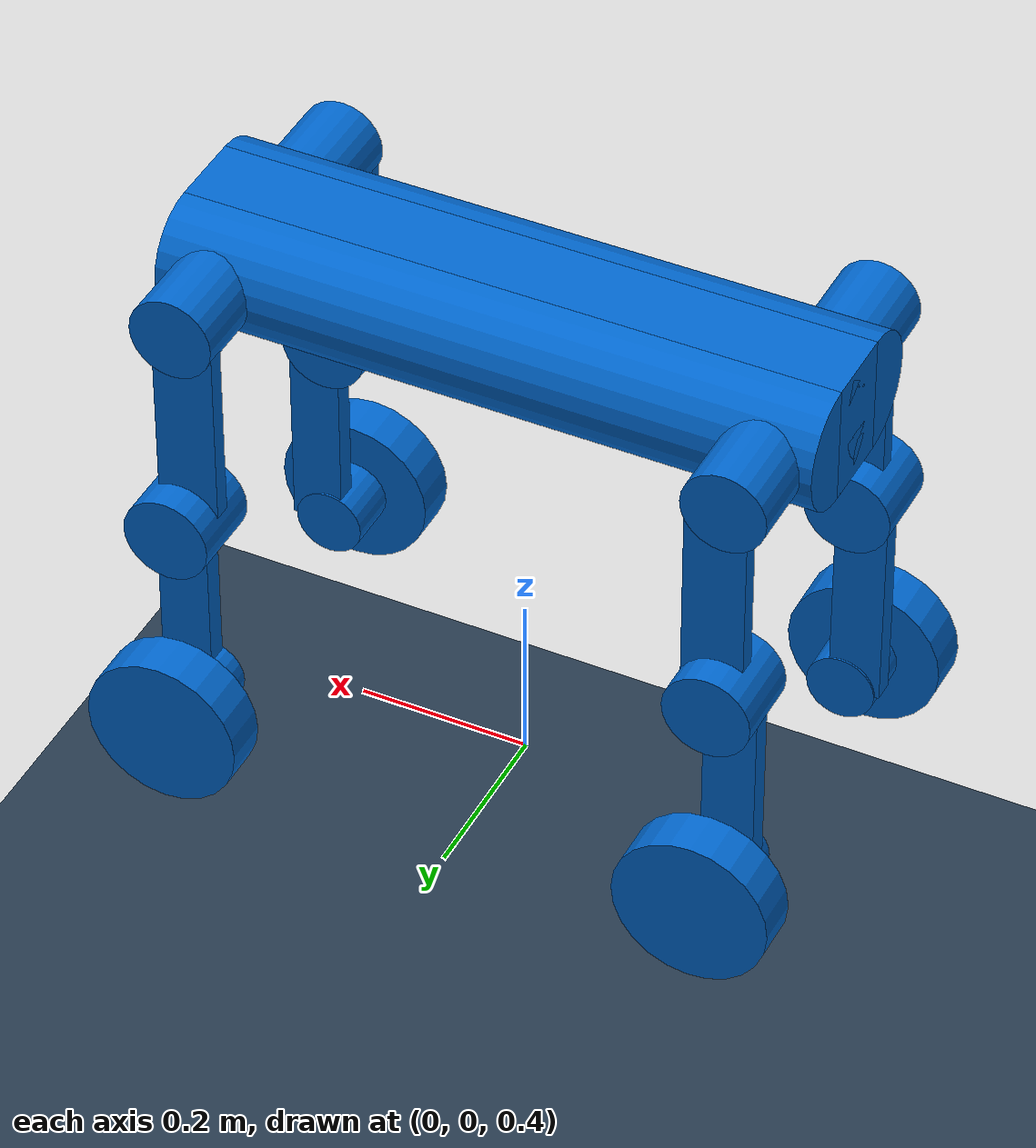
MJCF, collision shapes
<mujoco model="M20">
<visual>
  <quality
    shadowsize="16"
    offsamples="8"/>
</visual>

    <default>
        <default class="robot">
            <default class="motor">
                <joint/>
                <motor/>
            </default>
            <default class="visual">
                <geom material="default_material" type="mesh" contype="0" conaffinity="0" group="2"/>
            </default>
            <default class="collision">
                <geom material="collision_material" condim="3" contype="1" conaffinity="1" solref="0.005 1"
                      friction="1 0.01 0.001" density="0" group="1"/>
            </default>
        </default>
    </default>

    <compiler angle="radian" meshdir="../meshes/"/>
    <compiler autolimits="true"/>
    <include file="../meshes/base_link/base_link_assets.xml"/>
    <include file="../meshes/fl_hipx/fl_hipx_assets.xml"/>
    <include file="../meshes/fl_hipy/fl_hipy_assets.xml"/>
    <include file="../meshes/fl_knee/fl_knee_assets.xml"/>
    <include file="../meshes/fl_wheel/fl_wheel_assets.xml"/>

    <include file="../meshes/fr_hipx/fr_hipx_assets.xml"/>
    <include file="../meshes/fr_hipy/fr_hipy_assets.xml"/>
    <include file="../meshes/fr_knee/fr_knee_assets.xml"/>
    <include file="../meshes/fr_wheel/fr_wheel_assets.xml"/>

    <include file="../meshes/hl_hipx/hl_hipx_assets.xml"/>
    <include file="../meshes/hl_hipy/hl_hipy_assets.xml"/>
    <include file="../meshes/hl_knee/hl_knee_assets.xml"/>
    <include file="../meshes/hl_wheel/hl_wheel_assets.xml"/>

    <include file="../meshes/hr_hipx/hr_hipx_assets.xml"/>
    <include file="../meshes/hr_hipy/hr_hipy_assets.xml"/>
    <include file="../meshes/hr_knee/hr_knee_assets.xml"/>
    <include file="../meshes/hr_wheel/hr_wheel_assets.xml"/>

    <asset>
        <material name="default_material" rgba="0.7 0.7 0.7 1"/>
        <material name="collision_material" rgba="0.0 0.4 0.8 0.0"/>
        <texture name="texplane" type="2d" builtin="checker" rgb1=".2 .3 .4" rgb2=".1 0.15 0.2"
                 width="512" height="512"/>
        <material name='MatPlane' reflectance='0.3' texture="texplane" texrepeat="1 1" texuniform="true"/>
    </asset>

    <worldbody>
        <!-- 灯光 -->
        <light
        directional="true"
        castshadow="true"
        pos="-0.5 0.5 3"
        dir="0 0 -1"
        diffuse="0.9 0.9 0.9"
        specular="0.3 0.3 0.3"/>
        <geom name='floor' pos='0 0 0' size='100 100 .125' type='plane' material="MatPlane" condim='3'
              friction="1 0.01 0.01" group="0"/>

        <body name="base_link" pos="0 0. 1." quat="1 0 0 0" childclass="robot">
            <freejoint name="floating_base"/>
            <inertial pos="0.00355105878308153 0.0016507579200937 -0.00346462146571654"
                      quat="1 0 0 0"
                      mass="15.882" diaginertia="0.087919 0.533522 0.563492"/>

            <site name="imu_site" pos="0.0632 -0.0268 0.0435" size="0.005" rgba="1 0 0 1"/>
            <site name="base_site" pos="0 0 0" quat="1 0 0 0"/>

            <include file="../meshes/base_link/base_link_visual.xml"/>
            <geom size="0.375 0.045 0.07" type="box" class="collision"/>
            <geom size="0.07 0.375" pos="0 0.045 0" quat="0.707107 0 0.707107 0" type="cylinder" class="collision"/>
            <geom size="0.07 0.375" pos="0 -0.045 0" quat="0.707107 0 0.707107 0" type="cylinder" class="collision"/>

            <body name="fl_hipx" pos="0.3141 0.0685 0">
                <inertial pos="-0.0111893 0.00891693 0.000405666" quat="0.581628 0.481707 0.465607 0.461387"
                          mass="0.259964"
                          diaginertia="0.000374402 0.000286289 0.000179309"/>
                <joint name="fl_hipx_joint" pos="0 0 0" axis="-1 0 0" range="-0.436 0.611"
                       actuatorfrcrange="-76.4 76.4"/>
                <include file="../meshes/fl_hipx/fl_hipx_visual.xml"/>
                <geom size="0.048 0.07" pos="0 0.055 0" quat="0.707107 0.707107 0 0" type="cylinder" class="collision"/>
                <body name="fl_hipy">
                    <inertial pos="-0.00199375 0.098439 -0.130664" quat="0.6754 -0.0565887 0.0622156 0.73264"
                              mass="2.618"
                              diaginertia="0.0410181 0.0408067 0.00297328"/>
                    <joint name="fl_hipy_joint" pos="0 0 0" axis="0 -1 0" range="-2.286 2.583"
                           actuatorfrcrange="-76.4 76.4"/>
                    <include file="../meshes/fl_hipy/fl_hipy_visual.xml"/>
                    <geom size="0.035 0.01 0.125" pos="-0.01 0.11 -0.125" type="box" class="collision"/>
                    <geom size="0.05 0.045" pos="0 0.11 -0.25" quat="0.707107 0.707107 0 0" type="cylinder"
                          class="collision"/>
                    <body name="fl_knee" pos="0 0.0984 -0.25">
                        <inertial pos="0.00341917 0.00269124 -0.181265" quat="0.633405 -0.0508555 0.0475887 0.77068"
                                  mass="1.145" diaginertia="0.0121304 0.0117245 0.000948105"/>
                        <joint name="fl_knee_joint" pos="0 0 0" axis="0 -1 0" range="-2.809 2.792"
                               actuatorfrcrange="-76.4 76.4"/>
                        <include file="../meshes/fl_knee/fl_knee_visual.xml"/>
                        <geom size="0.03 0.0125 0.125" pos="0.015 -0.015 -0.125" type="box" class="collision"/>
                        <geom size="0.04 0.05" pos="0 0.02 -0.25" quat="0.707107 0.707107 0 0" type="cylinder"
                              class="collision"/>
                        <body name="fl_wheel" pos="0 0.059676 -0.25">
                            <inertial pos="-3.11398e-07 0.000279002 5.70329e-07" quat="0.707107 0 0 0.707107"
                                      mass="0.638"
                                      diaginertia="0.002853 0.001535 0.001535"/>
                            <joint name="fl_wheel_joint" pos="0 0 0" axis="0 -1 0" actuatorfrcrange="-21.6 21.6"/>
                            <include file="../meshes/fl_wheel/fl_wheel_visual.xml"/>
                            <geom size="0.09 0.027" quat="0.707107 0.707107 0 0" type="cylinder" class="collision"/>
                        </body>
                    </body>
                </body>
            </body>
            <body name="fr_hipx" pos="0.3141 -0.0685 0">
                <inertial pos="-0.0110901 -0.00875035 0.000521421" quat="0.461387 0.465607 0.481707 0.581628"
                          mass="0.259964" diaginertia="0.000374402 0.000286289 0.000179309"/>
                <joint name="fr_hipx_joint" pos="0 0 0" axis="-1 0 0" range="-0.611 0.436"
                       actuatorfrcrange="-76.4 76.4"/>
                <include file="../meshes/fr_hipx/fr_hipx_visual.xml"/>
                <geom size="0.048 0.07" pos="0 -0.055 0" quat="0.707107 0.707107 0 0" type="cylinder"
                      class="collision"/>
                <body name="fr_hipy">
                    <inertial pos="-0.00229992 -0.0989709 -0.130925" quat="0.6964 0.0586688 -0.0587886 0.712831"
                              mass="2.618" diaginertia="0.0407542 0.040538 0.00301281"/>
                    <joint name="fr_hipy_joint" pos="0 0 0" axis="0 -1 0" range="-2.286 2.583"
                           actuatorfrcrange="-76.4 76.4"/>
                    <include file="../meshes/fr_hipy/fr_hipy_visual.xml"/>
                    <geom size="0.035 0.01 0.125" pos="-0.01 -0.11 -0.125" type="box" class="collision"/>
                    <geom size="0.05 0.045" pos="0 -0.11 -0.25" quat="0.707107 0.707107 0 0" type="cylinder"
                          class="collision"/>
                    <body name="fr_knee" pos="0 -0.0984 -0.25">
                        <inertial pos="0.00354945 -0.00247884 -0.180089" quat="0.769194 0.0472982 -0.0504711 0.635261"
                                  mass="1.145" diaginertia="0.0122564 0.0118448 0.000951718"/>
                        <joint name="fr_knee_joint" pos="0 0 0" axis="0 -1 0" range="-2.809 2.792"
                               actuatorfrcrange="-76.4 76.4"/>
                        <include file="../meshes/fr_knee/fr_knee_visual.xml"/>
                        <geom size="0.03 0.0125 0.125" pos="0.015 0.015 -0.125" type="box" class="collision"/>
                        <geom size="0.04 0.05" pos="0 -0.02 -0.25" quat="0.707107 0.707107 0 0" type="cylinder"
                              class="collision"/>
                        <body name="fr_wheel" pos="0 -0.059676 -0.25">
                            <inertial pos="-6.47327e-07 -0.000279012 -4.6242e-08" quat="0.707107 0 0 0.707107"
                                      mass="0.638"
                                      diaginertia="0.002853 0.001535 0.001535"/>
                            <joint name="fr_wheel_joint" pos="0 0 0" axis="0 -1 0" actuatorfrcrange="-21.6 21.6"/>
                            <include file="../meshes/fr_wheel/fr_wheel_visual.xml"/>
                            <geom size="0.09 0.027" quat="0.707107 0.707107 0 0" type="cylinder" class="collision"/>
                        </body>
                    </body>
                </body>
            </body>
            <body name="hl_hipx" pos="-0.3141 0.0685 0">
                <inertial pos="0.0110901 0.00875014 0.000524884" quat="0.465607 0.461387 0.581628 0.481707"
                          mass="0.259964"
                          diaginertia="0.000374402 0.000286289 0.000179309"/>
                <joint name="hl_hipx_joint" pos="0 0 0" axis="-1 0 0" range="-0.436 0.611"
                       actuatorfrcrange="-76.4 76.4"/>
                <include file="../meshes/hl_hipx/hl_hipx_visual.xml"/>
                <geom size="0.048 0.07" pos="0 0.055 0" quat="0.707107 0.707107 0 0" type="cylinder" class="collision"/>
                <body name="hl_hipy">
                    <inertial pos="0.00204343 0.0990227 -0.130697" quat="0.750359 -0.0628584 0.0546506 0.655761"
                              mass="2.618" diaginertia="0.0408376 0.0406211 0.00299727"/>
                    <joint name="hl_hipy_joint" pos="0 0 0" axis="0 -1 0" range="-2.583 2.286"
                           actuatorfrcrange="-76.4 76.4"/>
                    <include file="../meshes/hl_hipy/hl_hipy_visual.xml"/>
                    <geom size="0.035 0.01 0.125" pos="0.01 0.11 -0.125" type="box" class="collision"/>
                    <geom size="0.05 0.045" pos="0 0.11 -0.25" quat="0.707107 0.707107 0 0" type="cylinder"
                          class="collision"/>
                    <body name="hl_knee" pos="0 0.0984 -0.25">
                        <inertial pos="-0.00354945 0.00247885 -0.180089" quat="0.769194 -0.0472982 0.0504711 0.635261"
                                  mass="1.145" diaginertia="0.0122564 0.0118448 0.000951718"/>
                        <joint name="hl_knee_joint" pos="0 0 0" axis="0 -1 0" range="-2.792 2.809"
                               actuatorfrcrange="-76.4 76.4"/>
                        <include file="../meshes/hl_knee/hl_knee_visual.xml"/>
                        <geom size="0.03 0.0125 0.125" pos="-0.015 0.015 -0.125" type="box" class="collision"/>
                        <geom size="0.04 0.05" pos="0 0.02 -0.25" quat="0.707107 0.707107 0 0" type="cylinder"
                              class="collision"/>
                        <body name="hl_wheel" pos="0 0.059676 -0.25">
                            <inertial pos="-6.07889e-07 0.000279009 2.1049e-07" quat="0.707107 0 0 0.707107"
                                      mass="0.638"
                                      diaginertia="0.002853 0.001535 0.001535"/>
                            <joint name="hl_wheel_joint" pos="0 0 0" axis="0 -1 0" actuatorfrcrange="-21.6 21.6"/>
                            <include file="../meshes/hl_wheel/hl_wheel_visual.xml"/>
                            <geom size="0.09 0.027" quat="0.707107 0.707107 0 0" type="cylinder" class="collision"/>
                        </body>
                    </body>
                </body>
            </body>
            <body name="hr_hipx" pos="-0.3141 -0.0685 0">
                <inertial pos="0.0110902 -0.00875012 0.000524937" quat="0.481707 0.581628 0.461387 0.465607"
                          mass="0.259964"
                          diaginertia="0.000374402 0.000286289 0.000179309"/>
                <joint name="hr_hipx_joint" pos="0 0 0" axis="-1 0 0" range="-0.611 0.436"
                       actuatorfrcrange="-76.4 76.4"/>
                <include file="../meshes/hr_hipx/hr_hipx_visual.xml"/>
                <geom size="0.048 0.07" pos="0 -0.055 0" quat="0.707107 0.707107 0 0" type="cylinder"
                      class="collision"/>
                <body name="hr_hipy">
                    <inertial pos="0.001992 -0.0983704 -0.130561" quat="0.676694 0.0567616 -0.0621797 0.731435"
                              mass="2.618"
                              diaginertia="0.0410109 0.0408028 0.00297526"/>
                    <joint name="hr_hipy_joint" pos="0 0 0" axis="0 -1 0" range="-2.583 2.286"
                           actuatorfrcrange="-76.4 76.4"/>
                    <include file="../meshes/hr_hipy/hr_hipy_visual.xml"/>
                    <geom size="0.035 0.01 0.125" pos="0.01 -0.11 -0.125" type="box" class="collision"/>
                    <geom size="0.05 0.045" pos="0 -0.11 -0.25" quat="0.707107 0.707107 0 0" type="cylinder"
                          class="collision"/>
                    <body name="hr_knee" pos="0 -0.0984 -0.25">
                        <inertial pos="-0.00341053 -0.00270202 -0.181287" quat="0.63448 0.050937 -0.0475303 0.769793"
                                  mass="1.145" diaginertia="0.0121352 0.0117289 0.000948904"/>
                        <joint name="hr_knee_joint" pos="0 0 0" axis="0 -1 0" range="-2.792 2.809"
                               actuatorfrcrange="-76.4 76.4"/>
                        <include file="../meshes/hr_knee/hr_knee_visual.xml"/>
                        <geom size="0.03 0.0125 0.125" pos="-0.015 0.015 -0.125" type="box" class="collision"/>
                        <geom size="0.04 0.05" pos="0 -0.02 -0.25" quat="0.707107 0.707107 0 0" type="cylinder"
                              class="collision"/>
                        <body name="hr_wheel" pos="0 -0.059676 -0.25">
                            <inertial pos="6.09746e-07 -0.000279009 2.01314e-07" quat="0.707107 0 0 0.707107"
                                      mass="0.638"
                                      diaginertia="0.002853 0.001535 0.001535"/>
                            <joint name="hr_wheel_joint" pos="0 0 0" axis="0 -1 0" actuatorfrcrange="-21.6 21.6"/>
                            <include file="../meshes/hr_wheel/hr_wheel_visual.xml"/>
                            <geom size="0.09 0.027" quat="0.707107 0.707107 0 0" type="cylinder" class="collision"/>
                        </body>
                    </body>
                </body>
            </body>
        </body>
    </worldbody>

    <actuator>
        <motor name="fl_hipx_joint" joint="fl_hipx_joint" ctrllimited="true" ctrlrange="-76.4 76.4" gear="1"/>
        <motor name="fl_hipy_joint" joint="fl_hipy_joint" ctrllimited="true" ctrlrange="-76.4 76.4" gear="1"/>
        <motor name="fl_knee_joint" joint="fl_knee_joint" ctrllimited="true" ctrlrange="-76.4 76.4" gear="1"/>
        <motor name="fl_wheel_joint" joint="fl_wheel_joint" ctrllimited="true" ctrlrange="-21.6 21.6" gear="1"/>
        <motor name="fr_hipx_joint" joint="fr_hipx_joint" ctrllimited="true" ctrlrange="-76.4 76.4" gear="1"/>
        <motor name="fr_hipy_joint" joint="fr_hipy_joint" ctrllimited="true" ctrlrange="-76.4 76.4" gear="1"/>
        <motor name="fr_knee_joint" joint="fr_knee_joint" ctrllimited="true" ctrlrange="-76.4 76.4" gear="1"/>
        <motor name="fr_wheel_joint" joint="fr_wheel_joint" ctrllimited="true" ctrlrange="-21.6 21.6" gear="1"/>
        <motor name="hl_hipx_joint" joint="hl_hipx_joint" ctrllimited="true" ctrlrange="-76.4 76.4" gear="1"/>
        <motor name="hl_hipy_joint" joint="hl_hipy_joint" ctrllimited="true" ctrlrange="-76.4 76.4" gear="1"/>
        <motor name="hl_knee_joint" joint="hl_knee_joint" ctrllimited="true" ctrlrange="-76.4 76.4" gear="1"/>
        <motor name="hl_wheel_joint" joint="hl_wheel_joint" ctrllimited="true" ctrlrange="-21.6 21.6" gear="1"/>
        <motor name="hr_hipx_joint" joint="hr_hipx_joint" ctrllimited="true" ctrlrange="-76.4 76.4" gear="1"/>
        <motor name="hr_hipy_joint" joint="hr_hipy_joint" ctrllimited="true" ctrlrange="-76.4 76.4" gear="1"/>
        <motor name="hr_knee_joint" joint="hr_knee_joint" ctrllimited="true" ctrlrange="-76.4 76.4" gear="1"/>
        <motor name="hr_wheel_joint" joint="hr_wheel_joint" ctrllimited="true" ctrlrange="-21.6 21.6" gear="1"/>
    </actuator>

    <contact>
        <exclude body1="base_link" body2="fl_hipx"/>
        <exclude body1="fl_hipx" body2="fl_hipy"/>
        <exclude body1="fl_hipy" body2="fl_knee"/>
        <exclude body1="fl_knee" body2="fl_wheel"/>

        <exclude body1="base_link" body2="fr_hipx"/>
        <exclude body1="fr_hipx" body2="fr_hipy"/>
        <exclude body1="fr_hipy" body2="fr_knee"/>
        <exclude body1="fr_knee" body2="fr_wheel"/>

        <exclude body1="base_link" body2="hl_hipx"/>
        <exclude body1="hl_hipx" body2="hl_hipy"/>
        <exclude body1="hl_hipy" body2="hl_knee"/>
        <exclude body1="hl_knee" body2="hl_wheel"/>

        <exclude body1="base_link" body2="hr_hipx"/>
        <exclude body1="hr_hipx" body2="hr_hipy"/>
        <exclude body1="hr_hipy" body2="hr_knee"/>
        <exclude body1="hr_knee" body2="hr_wheel"/>

    </contact>

    <sensor>
        <framequat name="base_quat" objtype="site" objname="base_site"/>
        <accelerometer site="imu_site"/>
        <gyro site="imu_site"/>

    </sensor>

    <keyframe>
        <key name="reset_pose" qpos="0  0  0.2  1 0 0 0  -0.438  -1.16  2.76  0  0.438  -1.16  2.76  0  -0.438  1.16  -2.76  0  0.438  1.16  -2.76  0"/>
    </keyframe>
</mujoco>

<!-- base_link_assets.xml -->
<mujoco>
  <asset>
    <material name="base_link/Material-7011塑胶" specular="0.5" shininess="0.25" rgba="0.309804 0.364706 0.419608 1.000000"/>
    <material name="base_link/Material-7011塑胶.001" specular="0.5" shininess="0.25" rgba="0.309804 0.364706 0.419608 1.000000"/>
    <material name="base_link/Material-7011塑胶.002" specular="0.5" shininess="0.25" rgba="0.309804 0.364706 0.419608 1.000000"/>
    <material name="base_link/Material-7011塑胶.003" specular="0.5" shininess="0.25" rgba="0.309804 0.364706 0.419608 1.000000"/>
    <material name="base_link/Material-7011油漆" specular="0.5" shininess="0.25" rgba="0.309804 0.364706 0.419608 1.000000"/>
    <material name="base_link/Material-7011油漆.001" specular="0.5" shininess="0.25" rgba="0.309804 0.364706 0.419608 1.000000"/>
    <material name="base_link/Material-7011油漆.002" specular="0.5" shininess="0.25" rgba="0.309804 0.364706 0.419608 1.000000"/>
    <material name="base_link/Material-7011油漆.003" specular="0.5" shininess="0.25" rgba="0.309804 0.364706 0.419608 1.000000"/>
    <material name="base_link/Material-7011油漆.004" specular="0.5" shininess="0.25" rgba="0.309804 0.364706 0.419608 1.000000"/>
    <material name="base_link/Material-7011油漆.005" specular="0.5" shininess="0.25" rgba="0.309804 0.364706 0.419608 1.000000"/>
    <material name="base_link/Material-7011油漆.006" specular="0.5" shininess="0.25" rgba="0.309804 0.364706 0.419608 1.000000"/>
    <material name="base_link/Material-7011油漆.007" specular="0.5" shininess="0.25" rgba="0.309804 0.364706 0.419608 1.000000"/>
    <material name="base_link/Material-7011油漆.008" specular="0.5" shininess="0.25" rgba="0.309804 0.364706 0.419608 1.000000"/>
    <material name="base_link/Material-7011油漆.009" specular="0.5" shininess="0.25" rgba="0.309804 0.364706 0.419608 1.000000"/>
    <material name="base_link/Material-7011油漆.010" specular="0.5" shininess="0.25" rgba="0.309804 0.364706 0.419608 1.000000"/>
    <material name="base_link/Material-7011油漆.011" specular="0.5" shininess="0.25" rgba="0.309804 0.364706 0.419608 1.000000"/>
    <material name="base_link/Material-7011油漆.012" specular="0.5" shininess="0.25" rgba="0.309804 0.364706 0.419608 1.000000"/>
    <material name="base_link/Material-7011油漆.013" specular="0.5" shininess="0.25" rgba="0.309804 0.364706 0.419608 1.000000"/>
    <material name="base_link/Material-7011油漆.014" specular="0.5" shininess="0.25" rgba="0.309804 0.364706 0.419608 1.000000"/>
    <material name="base_link/Material-7011油漆.015" specular="0.5" shininess="0.25" rgba="0.309804 0.364706 0.419608 1.000000"/>
    <material name="base_link/Material-7011油漆.016" specular="0.5" shininess="0.25" rgba="0.309804 0.364706 0.419608 1.000000"/>
    <material name="base_link/Material-7011油漆.017" specular="0.5" shininess="0.25" rgba="0.309804 0.364706 0.419608 1.000000"/>
    <material name="base_link/Material-7011油漆.018" specular="0.5" shininess="0.25" rgba="0.309804 0.364706 0.419608 1.000000"/>
    <material name="base_link/Material-7011油漆.019" specular="0.5" shininess="0.25" rgba="0.309804 0.364706 0.419608 1.000000"/>
    <material name="base_link/Material-7011油漆.020" specular="0.5" shininess="0.25" rgba="0.309804 0.364706 0.419608 1.000000"/>
    <material name="base_link/Material-7011油漆.021" specular="0.5" shininess="0.25" rgba="0.309804 0.364706 0.419608 1.000000"/>
    <material name="base_link/Material-7011油漆.022" specular="0.5" shininess="0.25" rgba="0.309804 0.364706 0.419608 1.000000"/>
    <material name="base_link/Material-7011油漆.023" specular="0.5" shininess="0.25" rgba="0.309804 0.364706 0.419608 1.000000"/>
    <material name="base_link/Material-7024油漆" specular="0.5" shininess="0.25" rgba="0.239216 0.290196 0.337255 1.000000"/>
    <material name="base_link/Material-7024油漆.001" specular="0.5" shininess="0.25" rgba="0.239216 0.290196 0.337255 1.000000"/>
    <material name="base_link/Material-7024油漆.002" specular="0.5" shininess="0.25" rgba="0.239216 0.290196 0.337255 1.000000"/>
    <material name="base_link/Material-7024油漆.003" specular="0.5" shininess="0.25" rgba="0.239216 0.290196 0.337255 1.000000"/>
    <material name="base_link/Material-7024油漆.004" specular="0.5" shininess="0.25" rgba="0.239216 0.290196 0.337255 1.000000"/>
    <material name="base_link/Material-7024油漆.005" specular="0.5" shininess="0.25" rgba="0.239216 0.290196 0.337255 1.000000"/>
    <material name="base_link/Material-7024油漆.006" specular="0.5" shininess="0.25" rgba="0.239216 0.290196 0.337255 1.000000"/>
    <material name="base_link/Material-7024油漆.007" specular="0.5" shininess="0.25" rgba="0.239216 0.290196 0.337255 1.000000"/>
    <material name="base_link/Material-7024油漆.008" specular="0.5" shininess="0.25" rgba="0.239216 0.290196 0.337255 1.000000"/>
    <material name="base_link/Material-7024油漆.009" specular="0.5" shininess="0.25" rgba="0.239216 0.290196 0.337255 1.000000"/>
    <material name="base_link/Material-7024油漆.010" specular="0.5" shininess="0.25" rgba="0.239216 0.290196 0.337255 1.000000"/>
    <material name="base_link/Material-7024油漆.011" specular="0.5" shininess="0.25" rgba="0.239216 0.290196 0.337255 1.000000"/>
    <material name="base_link/Material-7024油漆.012" specular="0.5" shininess="0.25" rgba="0.239216 0.290196 0.337255 1.000000"/>
    <material name="base_link/Material-塑胶" specular="0.5" shininess="0.25" rgba="0.000000 0.000000 0.000000 1.000000"/>
    <material name="base_link/Material-塑胶.001" specular="0.5" shininess="0.25" rgba="0.000000 0.000000 0.000000 1.000000"/>
    <material name="base_link/Material-塑胶__1_" specular="0.5" shininess="0.25" rgba="1.000000 1.000000 1.000000 0.610000"/>
    <material name="base_link/Material-塑胶__1_.001" specular="0.5" shininess="0.25" rgba="1.000000 1.000000 1.000000 0.610000"/>
    <material name="base_link/Material-塑胶__2_" specular="0.5" shininess="0.25" rgba="0.000000 0.000000 0.000000 1.000000"/>
    <material name="base_link/Material-塑胶__2_.001" specular="0.5" shininess="0.25" rgba="0.000000 0.000000 0.000000 1.000000"/>
    <material name="base_link/Material-塑胶__2_.002" specular="0.5" shininess="0.25" rgba="0.000000 0.000000 0.000000 1.000000"/>
    <material name="base_link/Material-塑胶__2_.003" specular="0.5" shininess="0.25" rgba="0.000000 0.000000 0.000000 1.000000"/>
    <material name="base_link/Material-塑胶__3_" specular="0.5" shininess="0.25" rgba="0.854902 0.850980 0.878431 1.000000"/>
    <material name="base_link/Material-塑胶__3_.001" specular="0.5" shininess="0.25" rgba="0.854902 0.850980 0.878431 1.000000"/>
    <material name="base_link/Material-塑胶__3_.002" specular="0.5" shininess="0.25" rgba="0.854902 0.850980 0.878431 1.000000"/>
    <material name="base_link/Material-塑胶__3_.003" specular="0.5" shininess="0.25" rgba="0.854902 0.850980 0.878431 1.000000"/>
    <material name="base_link/Material-塑胶__4_" specular="0.5" shininess="0.25" rgba="1.000000 0.000000 0.000000 1.000000"/>
    <material name="base_link/Material-塑胶__7_" specular="0.5" shininess="0.25" rgba="0.000000 0.000000 0.000000 1.000000"/>
    <material name="base_link/Material-塑胶__7_.001" specular="0.5" shininess="0.25" rgba="0.000000 0.000000 0.000000 1.000000"/>
    <material name="base_link/Material-塑胶__导入的_" specular="0.5" shininess="0.25" rgba="0.000000 0.000000 0.000000 1.000000"/>
    <material name="base_link/Material-塑胶__导入的_.001" specular="0.5" shininess="0.25" rgba="0.000000 0.000000 0.000000 1.000000"/>
    <material name="base_link/Material-塑胶__导入的_.002" specular="0.5" shininess="0.25" rgba="0.000000 0.000000 0.000000 1.000000"/>
    <material name="base_link/Material-金属__1_" specular="0.5" shininess="0.25" rgba="0.000000 0.000000 0.000000 1.000000"/>
    <mesh file="base_link_0.obj"/>
    <mesh file="base_link_1.obj"/>
    <mesh file="base_link_2.obj"/>
    <mesh file="base_link_3.obj"/>
    <mesh file="base_link_4.obj"/>
    <mesh file="base_link_5.obj"/>
    <mesh file="base_link_6.obj"/>
    <mesh file="base_link_7.obj"/>
    <mesh file="base_link_8.obj"/>
    <mesh file="base_link_9.obj"/>
    <mesh file="base_link_10.obj"/>
    <mesh file="base_link_11.obj"/>
    <mesh file="base_link_12.obj"/>
    <mesh file="base_link_13.obj"/>
    <mesh file="base_link_14.obj"/>
    <mesh file="base_link_15.obj"/>
    <mesh file="base_link_16.obj"/>
    <mesh file="base_link_17.obj"/>
    <mesh file="base_link_18.obj"/>
    <mesh file="base_link_19.obj"/>
    <mesh file="base_link_20.obj"/>
    <mesh file="base_link_21.obj"/>
    <mesh file="base_link_22.obj"/>
    <mesh file="base_link_23.obj"/>
    <mesh file="base_link_24.obj"/>
    <mesh file="base_link_25.obj"/>
    <mesh file="base_link_26.obj"/>
    <mesh file="base_link_27.obj"/>
    <mesh file="base_link_28.obj"/>
    <mesh file="base_link_29.obj"/>
    <mesh file="base_link_30.obj"/>
    <mesh file="base_link_31.obj"/>
    <mesh file="base_link_32.obj"/>
    <mesh file="base_link_33.obj"/>
    <mesh file="base_link_34.obj"/>
    <mesh file="base_link_35.obj"/>
    <mesh file="base_link_36.obj"/>
    <mesh file="base_link_37.obj"/>
    <mesh file="base_link_38.obj"/>
    <mesh file="base_link_39.obj"/>
    <mesh file="base_link_40.obj"/>
    <mesh file="base_link_41.obj"/>
    <mesh file="base_link_42.obj"/>
    <mesh file="base_link_43.obj"/>
    <mesh file="base_link_44.obj"/>
    <mesh file="base_link_45.obj"/>
    <mesh file="base_link_46.obj"/>
    <mesh file="base_link_47.obj"/>
    <mesh file="base_link_48.obj"/>
    <mesh file="base_link_49.obj"/>
    <mesh file="base_link_50.obj"/>
    <mesh file="base_link_51.obj"/>
    <mesh file="base_link_52.obj"/>
    <mesh file="base_link_53.obj"/>
    <mesh file="base_link_54.obj"/>
    <mesh file="base_link_55.obj"/>
    <mesh file="base_link_56.obj"/>
    <mesh file="base_link_57.obj"/>
    <mesh file="base_link_58.obj"/>
    <mesh file="base_link_59.obj"/>
  </asset>

</mujoco>

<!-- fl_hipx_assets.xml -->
<mujoco>
  <asset>
    <material name="fl_hipx/Material-7024油漆" specular="0.5" shininess="0.25" rgba="0.239216 0.290196 0.337255 1.000000"/>
    <mesh file="fl_hipx.obj"/>
  </asset>
</mujoco>

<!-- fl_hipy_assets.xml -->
<mujoco>
  <asset>
    <material name="fl_hipy/Material-7011油漆" specular="0.5" shininess="0.25" rgba="0.309804 0.364706 0.419608 1.000000"/>
    <material name="fl_hipy/Material-7011油漆.001" specular="0.5" shininess="0.25" rgba="0.309804 0.364706 0.419608 1.000000"/>
    <material name="fl_hipy/Material-7011油漆.002" specular="0.5" shininess="0.25" rgba="0.309804 0.364706 0.419608 1.000000"/>
    <material name="fl_hipy/Material-7011油漆.003" specular="0.5" shininess="0.25" rgba="0.309804 0.364706 0.419608 1.000000"/>
    <material name="fl_hipy/Material-7011油漆.004" specular="0.5" shininess="0.25" rgba="0.309804 0.364706 0.419608 1.000000"/>
    <material name="fl_hipy/Material-7011油漆.005" specular="0.5" shininess="0.25" rgba="0.309804 0.364706 0.419608 1.000000"/>
    <material name="fl_hipy/Material-7011油漆.006" specular="0.5" shininess="0.25" rgba="0.309804 0.364706 0.419608 1.000000"/>
    <material name="fl_hipy/Material-7011油漆.007" specular="0.5" shininess="0.25" rgba="0.309804 0.364706 0.419608 1.000000"/>
    <material name="fl_hipy/Material-7011油漆.008" specular="0.5" shininess="0.25" rgba="0.309804 0.364706 0.419608 1.000000"/>
    <material name="fl_hipy/Material-7011油漆.009" specular="0.5" shininess="0.25" rgba="0.309804 0.364706 0.419608 1.000000"/>
    <material name="fl_hipy/Material-7011油漆.010" specular="0.5" shininess="0.25" rgba="0.309804 0.364706 0.419608 1.000000"/>
    <material name="fl_hipy/Material-7011油漆.011" specular="0.5" shininess="0.25" rgba="0.309804 0.364706 0.419608 1.000000"/>
    <material name="fl_hipy/Material-7011油漆.012" specular="0.5" shininess="0.25" rgba="0.309804 0.364706 0.419608 1.000000"/>
    <material name="fl_hipy/Material-7011油漆.013" specular="0.5" shininess="0.25" rgba="0.309804 0.364706 0.419608 1.000000"/>
    <material name="fl_hipy/Material-7011油漆.014" specular="0.5" shininess="0.25" rgba="0.309804 0.364706 0.419608 1.000000"/>
    <material name="fl_hipy/Material-7011油漆.015" specular="0.5" shininess="0.25" rgba="0.309804 0.364706 0.419608 1.000000"/>
    <material name="fl_hipy/Material-7011油漆.016" specular="0.5" shininess="0.25" rgba="0.309804 0.364706 0.419608 1.000000"/>
    <material name="fl_hipy/Material-7011油漆.017" specular="0.5" shininess="0.25" rgba="0.309804 0.364706 0.419608 1.000000"/>
    <material name="fl_hipy/Material-7011油漆.018" specular="0.5" shininess="0.25" rgba="0.309804 0.364706 0.419608 1.000000"/>
    <material name="fl_hipy/Material-7011油漆.019" specular="0.5" shininess="0.25" rgba="0.309804 0.364706 0.419608 1.000000"/>
    <material name="fl_hipy/Material-7011油漆.020" specular="0.5" shininess="0.25" rgba="0.309804 0.364706 0.419608 1.000000"/>
    <material name="fl_hipy/Material-7011油漆.021" specular="0.5" shininess="0.25" rgba="0.309804 0.364706 0.419608 1.000000"/>
    <material name="fl_hipy/Material-7011油漆.022" specular="0.5" shininess="0.25" rgba="0.309804 0.364706 0.419608 1.000000"/>
    <material name="fl_hipy/Material-7011油漆.023" specular="0.5" shininess="0.25" rgba="0.309804 0.364706 0.419608 1.000000"/>
    <material name="fl_hipy/Material-7011油漆.024" specular="0.5" shininess="0.25" rgba="0.309804 0.364706 0.419608 1.000000"/>
    <material name="fl_hipy/Material-7011油漆.025" specular="0.5" shininess="0.25" rgba="0.309804 0.364706 0.419608 1.000000"/>
    <material name="fl_hipy/Material-7011油漆.026" specular="0.5" shininess="0.25" rgba="0.309804 0.364706 0.419608 1.000000"/>
    <material name="fl_hipy/Material-7011油漆.027" specular="0.5" shininess="0.25" rgba="0.309804 0.364706 0.419608 1.000000"/>
    <material name="fl_hipy/Material-7011油漆.028" specular="0.5" shininess="0.25" rgba="0.309804 0.364706 0.419608 1.000000"/>
    <material name="fl_hipy/Material-7011油漆.029" specular="0.5" shininess="0.25" rgba="0.309804 0.364706 0.419608 1.000000"/>
    <material name="fl_hipy/Material-7011油漆.030" specular="0.5" shininess="0.25" rgba="0.309804 0.364706 0.419608 1.000000"/>
    <material name="fl_hipy/Material-7011油漆.031" specular="0.5" shininess="0.25" rgba="0.309804 0.364706 0.419608 1.000000"/>
    <material name="fl_hipy/Material-7011油漆.032" specular="0.5" shininess="0.25" rgba="0.309804 0.364706 0.419608 1.000000"/>
    <material name="fl_hipy/Material-7011油漆.033" specular="0.5" shininess="0.25" rgba="0.309804 0.364706 0.419608 1.000000"/>
    <material name="fl_hipy/Material-7024塑胶" specular="0.5" shininess="0.25" rgba="0.239216 0.290196 0.337255 1.000000"/>
    <material name="fl_hipy/Material-塑胶" specular="0.5" shininess="0.25" rgba="0.000000 0.000000 0.000000 1.000000"/>
    <material name="fl_hipy/Material-塑胶__3_" specular="0.5" shininess="0.25" rgba="0.854902 0.850980 0.878431 1.000000"/>
    <material name="fl_hipy/Material-塑胶__3_.001" specular="0.5" shininess="0.25" rgba="0.854902 0.850980 0.878431 1.000000"/>
    <material name="fl_hipy/Material-塑胶__3_.002" specular="0.5" shininess="0.25" rgba="0.854902 0.850980 0.878431 1.000000"/>
    <material name="fl_hipy/Material-油漆" specular="0.5" shininess="0.25" rgba="0.854902 0.850980 0.878431 1.000000"/>
    <material name="a0000000-0000-0000-0000-000000000000" specular="0.5" shininess="0.25" rgba="0.980392 0.980392 0.980392 1.000000"/>
    <mesh file="fl_hipy_0.obj"/>
    <mesh file="fl_hipy_1.obj"/>
    <mesh file="fl_hipy_2.obj"/>
    <mesh file="fl_hipy_3.obj"/>
    <mesh file="fl_hipy_4.obj"/>
    <mesh file="fl_hipy_5.obj"/>
    <mesh file="fl_hipy_6.obj"/>
    <mesh file="fl_hipy_7.obj"/>
    <mesh file="fl_hipy_8.obj"/>
    <mesh file="fl_hipy_9.obj"/>
    <mesh file="fl_hipy_10.obj"/>
    <mesh file="fl_hipy_11.obj"/>
    <mesh file="fl_hipy_12.obj"/>
    <mesh file="fl_hipy_13.obj"/>
    <mesh file="fl_hipy_14.obj"/>
    <mesh file="fl_hipy_15.obj"/>
    <mesh file="fl_hipy_16.obj"/>
    <mesh file="fl_hipy_17.obj"/>
    <mesh file="fl_hipy_18.obj"/>
    <mesh file="fl_hipy_19.obj"/>
    <mesh file="fl_hipy_20.obj"/>
    <mesh file="fl_hipy_21.obj"/>
    <mesh file="fl_hipy_22.obj"/>
    <mesh file="fl_hipy_23.obj"/>
    <mesh file="fl_hipy_24.obj"/>
    <mesh file="fl_hipy_25.obj"/>
    <mesh file="fl_hipy_26.obj"/>
    <mesh file="fl_hipy_27.obj"/>
    <mesh file="fl_hipy_28.obj"/>
    <mesh file="fl_hipy_29.obj"/>
    <mesh file="fl_hipy_30.obj"/>
    <mesh file="fl_hipy_31.obj"/>
    <mesh file="fl_hipy_32.obj"/>
    <mesh file="fl_hipy_33.obj"/>
    <mesh file="fl_hipy_34.obj"/>
    <mesh file="fl_hipy_35.obj"/>
    <mesh file="fl_hipy_36.obj"/>
    <mesh file="fl_hipy_37.obj"/>
    <mesh file="fl_hipy_38.obj"/>
    <mesh file="fl_hipy_39.obj"/>
    <mesh file="fl_hipy_40.obj"/>
  </asset>
</mujoco>

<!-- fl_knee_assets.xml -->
<mujoco>
  <asset>
    <material name="fl_knee/Material-7011油漆" specular="0.5" shininess="0.25" rgba="0.309804 0.364706 0.419608 1.000000"/>
    <material name="fl_knee/Material-7011油漆.001" specular="0.5" shininess="0.25" rgba="0.309804 0.364706 0.419608 1.000000"/>
    <material name="fl_knee/Material-7024塑胶" specular="0.5" shininess="0.25" rgba="0.239216 0.290196 0.337255 1.000000"/>
    <material name="fl_knee/Material-7024油漆" specular="0.5" shininess="0.25" rgba="0.239216 0.290196 0.337255 1.000000"/>
    <material name="fl_knee/Material-7024油漆.001" specular="0.5" shininess="0.25" rgba="0.239216 0.290196 0.337255 1.000000"/>
    <mesh file="fl_knee_0.obj"/>
    <mesh file="fl_knee_1.obj"/>
    <mesh file="fl_knee_2.obj"/>
    <mesh file="fl_knee_3.obj"/>
    <mesh file="fl_knee_4.obj"/>
  </asset>

</mujoco>

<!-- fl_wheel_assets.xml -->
<mujoco>
  <asset>
    <material name="fl_wheel/Material-7011油漆" specular="0.5" shininess="0.25" rgba="0.309804 0.364706 0.419608 1.000000"/>
    <material name="fl_wheel/Material-7011油漆.001" specular="0.5" shininess="0.25" rgba="0.309804 0.364706 0.419608 1.000000"/>
    <material name="fl_wheel/Material-7011油漆.002" specular="0.5" shininess="0.25" rgba="0.309804 0.364706 0.419608 1.000000"/>
    <material name="fl_wheel/Material-7011油漆.003" specular="0.5" shininess="0.25" rgba="0.309804 0.364706 0.419608 1.000000"/>
    <material name="fl_wheel/Material-7011油漆.004" specular="0.5" shininess="0.25" rgba="0.309804 0.364706 0.419608 1.000000"/>
    <material name="fl_wheel/Material-7011油漆.005" specular="0.5" shininess="0.25" rgba="0.309804 0.364706 0.419608 1.000000"/>
    <material name="fl_wheel/Material-7011油漆.006" specular="0.5" shininess="0.25" rgba="0.309804 0.364706 0.419608 1.000000"/>
    <material name="fl_wheel/Material-塑胶" specular="0.5" shininess="0.25" rgba="0.000000 0.000000 0.000000 1.000000"/>
    <material name="fl_wheel/Material-塑胶.001" specular="0.5" shininess="0.25" rgba="0.000000 0.000000 0.000000 1.000000"/>
    <material name="fl_wheel/Material-塑胶__3_" specular="0.5" shininess="0.25" rgba="0.854902 0.850980 0.878431 1.000000"/>
    <mesh file="fl_wheel_0.obj"/>
    <mesh file="fl_wheel_1.obj"/>
    <mesh file="fl_wheel_2.obj"/>
    <mesh file="fl_wheel_3.obj"/>
    <mesh file="fl_wheel_4.obj"/>
    <mesh file="fl_wheel_5.obj"/>
    <mesh file="fl_wheel_6.obj"/>
    <mesh file="fl_wheel_7.obj"/>
    <mesh file="fl_wheel_8.obj"/>
    <mesh file="fl_wheel_9.obj"/>
  </asset>
</mujoco>

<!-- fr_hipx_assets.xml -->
<mujoco>
  <asset>
    <material name="fr_hipx/Material-7024油漆" specular="0.5" shininess="0.25" rgba="0.239216 0.290196 0.337255 1.000000"/>
    <mesh file="fr_hipx.obj"/>
  </asset>
</mujoco>

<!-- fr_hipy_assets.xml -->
<mujoco>
  <asset>
    <material name="fr_hipy/Material-7011油漆" specular="0.5" shininess="0.25" rgba="0.309804 0.364706 0.419608 1.000000"/>
    <material name="fr_hipy/Material-7011油漆.001" specular="0.5" shininess="0.25" rgba="0.309804 0.364706 0.419608 1.000000"/>
    <material name="fr_hipy/Material-7011油漆.002" specular="0.5" shininess="0.25" rgba="0.309804 0.364706 0.419608 1.000000"/>
    <material name="fr_hipy/Material-7011油漆.003" specular="0.5" shininess="0.25" rgba="0.309804 0.364706 0.419608 1.000000"/>
    <material name="fr_hipy/Material-7011油漆.004" specular="0.5" shininess="0.25" rgba="0.309804 0.364706 0.419608 1.000000"/>
    <material name="fr_hipy/Material-7011油漆.005" specular="0.5" shininess="0.25" rgba="0.309804 0.364706 0.419608 1.000000"/>
    <material name="fr_hipy/Material-7011油漆.006" specular="0.5" shininess="0.25" rgba="0.309804 0.364706 0.419608 1.000000"/>
    <material name="fr_hipy/Material-7011油漆.007" specular="0.5" shininess="0.25" rgba="0.309804 0.364706 0.419608 1.000000"/>
    <material name="fr_hipy/Material-7011油漆.008" specular="0.5" shininess="0.25" rgba="0.309804 0.364706 0.419608 1.000000"/>
    <material name="fr_hipy/Material-7011油漆.009" specular="0.5" shininess="0.25" rgba="0.309804 0.364706 0.419608 1.000000"/>
    <material name="fr_hipy/Material-7011油漆.010" specular="0.5" shininess="0.25" rgba="0.309804 0.364706 0.419608 1.000000"/>
    <material name="fr_hipy/Material-7011油漆.011" specular="0.5" shininess="0.25" rgba="0.309804 0.364706 0.419608 1.000000"/>
    <material name="fr_hipy/Material-7011油漆.012" specular="0.5" shininess="0.25" rgba="0.309804 0.364706 0.419608 1.000000"/>
    <material name="fr_hipy/Material-7011油漆.013" specular="0.5" shininess="0.25" rgba="0.309804 0.364706 0.419608 1.000000"/>
    <material name="fr_hipy/Material-7011油漆.014" specular="0.5" shininess="0.25" rgba="0.309804 0.364706 0.419608 1.000000"/>
    <material name="fr_hipy/Material-7011油漆.015" specular="0.5" shininess="0.25" rgba="0.309804 0.364706 0.419608 1.000000"/>
    <material name="fr_hipy/Material-7011油漆.016" specular="0.5" shininess="0.25" rgba="0.309804 0.364706 0.419608 1.000000"/>
    <material name="fr_hipy/Material-7011油漆.017" specular="0.5" shininess="0.25" rgba="0.309804 0.364706 0.419608 1.000000"/>
    <material name="fr_hipy/Material-7011油漆.018" specular="0.5" shininess="0.25" rgba="0.309804 0.364706 0.419608 1.000000"/>
    <material name="fr_hipy/Material-7011油漆.019" specular="0.5" shininess="0.25" rgba="0.309804 0.364706 0.419608 1.000000"/>
    <material name="fr_hipy/Material-7011油漆.020" specular="0.5" shininess="0.25" rgba="0.309804 0.364706 0.419608 1.000000"/>
    <material name="fr_hipy/Material-7011油漆.021" specular="0.5" shininess="0.25" rgba="0.309804 0.364706 0.419608 1.000000"/>
    <material name="fr_hipy/Material-7011油漆.022" specular="0.5" shininess="0.25" rgba="0.309804 0.364706 0.419608 1.000000"/>
    <material name="fr_hipy/Material-7011油漆.023" specular="0.5" shininess="0.25" rgba="0.309804 0.364706 0.419608 1.000000"/>
    <material name="fr_hipy/Material-7011油漆.024" specular="0.5" shininess="0.25" rgba="0.309804 0.364706 0.419608 1.000000"/>
    <material name="fr_hipy/Material-7011油漆.025" specular="0.5" shininess="0.25" rgba="0.309804 0.364706 0.419608 1.000000"/>
    <material name="fr_hipy/Material-7011油漆.026" specular="0.5" shininess="0.25" rgba="0.309804 0.364706 0.419608 1.000000"/>
    <material name="fr_hipy/Material-7011油漆.027" specular="0.5" shininess="0.25" rgba="0.309804 0.364706 0.419608 1.000000"/>
    <material name="fr_hipy/Material-7011油漆.028" specular="0.5" shininess="0.25" rgba="0.309804 0.364706 0.419608 1.000000"/>
    <material name="fr_hipy/Material-7011油漆.029" specular="0.5" shininess="0.25" rgba="0.309804 0.364706 0.419608 1.000000"/>
    <material name="fr_hipy/Material-7011油漆.030" specular="0.5" shininess="0.25" rgba="0.309804 0.364706 0.419608 1.000000"/>
    <material name="fr_hipy/Material-7011油漆.031" specular="0.5" shininess="0.25" rgba="0.309804 0.364706 0.419608 1.000000"/>
    <material name="fr_hipy/Material-7011油漆.032" specular="0.5" shininess="0.25" rgba="0.309804 0.364706 0.419608 1.000000"/>
    <material name="fr_hipy/Material-7011油漆.033" specular="0.5" shininess="0.25" rgba="0.309804 0.364706 0.419608 1.000000"/>
    <material name="fr_hipy/Material-7011油漆.034" specular="0.5" shininess="0.25" rgba="0.309804 0.364706 0.419608 1.000000"/>
    <material name="fr_hipy/Material-7011油漆.035" specular="0.5" shininess="0.25" rgba="0.309804 0.364706 0.419608 1.000000"/>
    <material name="fr_hipy/Material-7011油漆.036" specular="0.5" shininess="0.25" rgba="0.309804 0.364706 0.419608 1.000000"/>
    <material name="fr_hipy/Material-7011油漆.037" specular="0.5" shininess="0.25" rgba="0.309804 0.364706 0.419608 1.000000"/>
    <material name="fr_hipy/Material-7011油漆.038" specular="0.5" shininess="0.25" rgba="0.309804 0.364706 0.419608 1.000000"/>
    <material name="fr_hipy/Material-7024塑胶" specular="0.5" shininess="0.25" rgba="0.239216 0.290196 0.337255 1.000000"/>
    <material name="fr_hipy/Material-塑胶" specular="0.5" shininess="0.25" rgba="0.000000 0.000000 0.000000 1.000000"/>
    <material name="fr_hipy/Material-塑胶__3_" specular="0.5" shininess="0.25" rgba="0.854902 0.850980 0.878431 1.000000"/>
    <material name="fr_hipy/Material-油漆" specular="0.5" shininess="0.25" rgba="0.854902 0.850980 0.878431 1.000000"/>
    <mesh file="fr_hipy_0.obj"/>
    <mesh file="fr_hipy_1.obj"/>
    <mesh file="fr_hipy_2.obj"/>
    <mesh file="fr_hipy_3.obj"/>
    <mesh file="fr_hipy_4.obj"/>
    <mesh file="fr_hipy_5.obj"/>
    <mesh file="fr_hipy_6.obj"/>
    <mesh file="fr_hipy_7.obj"/>
    <mesh file="fr_hipy_8.obj"/>
    <mesh file="fr_hipy_9.obj"/>
    <mesh file="fr_hipy_10.obj"/>
    <mesh file="fr_hipy_11.obj"/>
    <mesh file="fr_hipy_12.obj"/>
    <mesh file="fr_hipy_13.obj"/>
    <mesh file="fr_hipy_14.obj"/>
    <mesh file="fr_hipy_15.obj"/>
    <mesh file="fr_hipy_16.obj"/>
    <mesh file="fr_hipy_17.obj"/>
    <mesh file="fr_hipy_18.obj"/>
    <mesh file="fr_hipy_19.obj"/>
    <mesh file="fr_hipy_20.obj"/>
    <mesh file="fr_hipy_21.obj"/>
    <mesh file="fr_hipy_22.obj"/>
    <mesh file="fr_hipy_23.obj"/>
    <mesh file="fr_hipy_24.obj"/>
    <mesh file="fr_hipy_25.obj"/>
    <mesh file="fr_hipy_26.obj"/>
    <mesh file="fr_hipy_27.obj"/>
    <mesh file="fr_hipy_28.obj"/>
    <mesh file="fr_hipy_29.obj"/>
    <mesh file="fr_hipy_30.obj"/>
    <mesh file="fr_hipy_31.obj"/>
    <mesh file="fr_hipy_32.obj"/>
    <mesh file="fr_hipy_33.obj"/>
    <mesh file="fr_hipy_34.obj"/>
    <mesh file="fr_hipy_35.obj"/>
    <mesh file="fr_hipy_36.obj"/>
    <mesh file="fr_hipy_37.obj"/>
    <mesh file="fr_hipy_38.obj"/>
    <mesh file="fr_hipy_39.obj"/>
    <mesh file="fr_hipy_40.obj"/>
    <mesh file="fr_hipy_41.obj"/>
    <mesh file="fr_hipy_42.obj"/>
  </asset>
</mujoco>

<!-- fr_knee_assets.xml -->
<mujoco>
  <asset>
    <material name="fr_knee/Material-7011油漆" specular="0.5" shininess="0.25" rgba="0.309804 0.364706 0.419608 1.000000"/>
    <material name="fr_knee/Material-7011油漆.001" specular="0.5" shininess="0.25" rgba="0.309804 0.364706 0.419608 1.000000"/>
    <material name="fr_knee/Material-7024塑胶" specular="0.5" shininess="0.25" rgba="0.239216 0.290196 0.337255 1.000000"/>
    <material name="fr_knee/Material-7024油漆" specular="0.5" shininess="0.25" rgba="0.239216 0.290196 0.337255 1.000000"/>
    <material name="fr_knee/Material-7024油漆.001" specular="0.5" shininess="0.25" rgba="0.239216 0.290196 0.337255 1.000000"/>
    <mesh file="fr_knee_0.obj"/>
    <mesh file="fr_knee_1.obj"/>
    <mesh file="fr_knee_2.obj"/>
    <mesh file="fr_knee_3.obj"/>
    <mesh file="fr_knee_4.obj"/>
  </asset>
</mujoco>

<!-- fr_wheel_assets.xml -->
<mujoco>
  <asset>
    <material name="fr_wheel/Material-7011油漆" specular="0.5" shininess="0.25" rgba="0.309804 0.364706 0.419608 1.000000"/>
    <material name="fr_wheel/Material-7011油漆.001" specular="0.5" shininess="0.25" rgba="0.309804 0.364706 0.419608 1.000000"/>
    <material name="fr_wheel/Material-7011油漆.002" specular="0.5" shininess="0.25" rgba="0.309804 0.364706 0.419608 1.000000"/>
    <material name="fr_wheel/Material-7011油漆.003" specular="0.5" shininess="0.25" rgba="0.309804 0.364706 0.419608 1.000000"/>
    <material name="fr_wheel/Material-7011油漆.004" specular="0.5" shininess="0.25" rgba="0.309804 0.364706 0.419608 1.000000"/>
    <material name="fr_wheel/Material-7011油漆.005" specular="0.5" shininess="0.25" rgba="0.309804 0.364706 0.419608 1.000000"/>
    <material name="fr_wheel/Material-7011油漆.006" specular="0.5" shininess="0.25" rgba="0.309804 0.364706 0.419608 1.000000"/>
    <material name="fr_wheel/Material-塑胶" specular="0.5" shininess="0.25" rgba="0.000000 0.000000 0.000000 1.000000"/>
    <material name="fr_wheel/Material-塑胶__3_" specular="0.5" shininess="0.25" rgba="0.854902 0.850980 0.878431 1.000000"/>
    <mesh file="fr_wheel_0.obj"/>
    <mesh file="fr_wheel_1.obj"/>
    <mesh file="fr_wheel_2.obj"/>
    <mesh file="fr_wheel_3.obj"/>
    <mesh file="fr_wheel_4.obj"/>
    <mesh file="fr_wheel_5.obj"/>
    <mesh file="fr_wheel_6.obj"/>
    <mesh file="fr_wheel_7.obj"/>
    <mesh file="fr_wheel_8.obj"/>
  </asset>
</mujoco>

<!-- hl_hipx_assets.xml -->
<mujoco>
  <asset>
    <material name="hl_hipx/Material-7024油漆" specular="0.5" shininess="0.25" rgba="0.239216 0.290196 0.337255 1.000000"/>
    <mesh file="hl_hipx.obj"/>
  </asset>
</mujoco>

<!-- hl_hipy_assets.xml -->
<mujoco>
  <asset>
    <material name="hl_hipy/Material-7011塑胶" specular="0.5" shininess="0.25" rgba="0.309804 0.364706 0.419608 1.000000"/>
    <material name="hl_hipy/Material-7011油漆" specular="0.5" shininess="0.25" rgba="0.309804 0.364706 0.419608 1.000000"/>
    <material name="hl_hipy/Material-7011油漆.001" specular="0.5" shininess="0.25" rgba="0.309804 0.364706 0.419608 1.000000"/>
    <material name="hl_hipy/Material-7011油漆.002" specular="0.5" shininess="0.25" rgba="0.309804 0.364706 0.419608 1.000000"/>
    <material name="hl_hipy/Material-7011油漆.003" specular="0.5" shininess="0.25" rgba="0.309804 0.364706 0.419608 1.000000"/>
    <material name="hl_hipy/Material-7011油漆.004" specular="0.5" shininess="0.25" rgba="0.309804 0.364706 0.419608 1.000000"/>
    <material name="hl_hipy/Material-7011油漆.005" specular="0.5" shininess="0.25" rgba="0.309804 0.364706 0.419608 1.000000"/>
    <material name="hl_hipy/Material-7011油漆.006" specular="0.5" shininess="0.25" rgba="0.309804 0.364706 0.419608 1.000000"/>
    <material name="hl_hipy/Material-7024塑胶" specular="0.5" shininess="0.25" rgba="0.239216 0.290196 0.337255 1.000000"/>
    <material name="hl_hipy/Material-塑胶" specular="0.5" shininess="0.25" rgba="0.000000 0.000000 0.000000 1.000000"/>
    <mesh file="hl_hipy_0.obj"/>
    <mesh file="hl_hipy_1.obj"/>
    <mesh file="hl_hipy_2.obj"/>
    <mesh file="hl_hipy_3.obj"/>
    <mesh file="hl_hipy_4.obj"/>
    <mesh file="hl_hipy_5.obj"/>
    <mesh file="hl_hipy_6.obj"/>
    <mesh file="hl_hipy_7.obj"/>
    <mesh file="hl_hipy_8.obj"/>
    <mesh file="hl_hipy_9.obj"/>
  </asset>
</mujoco>

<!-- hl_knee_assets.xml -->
<mujoco>
  <asset>
    <material name="hl_knee/Material-7011油漆" specular="0.5" shininess="0.25" rgba="0.309804 0.364706 0.419608 1.000000"/>
    <material name="hl_knee/Material-7011油漆.001" specular="0.5" shininess="0.25" rgba="0.309804 0.364706 0.419608 1.000000"/>
    <material name="hl_knee/Material-7024塑胶" specular="0.5" shininess="0.25" rgba="0.239216 0.290196 0.337255 1.000000"/>
    <material name="hl_knee/Material-7024油漆" specular="0.5" shininess="0.25" rgba="0.239216 0.290196 0.337255 1.000000"/>
    <mesh file="hl_knee_0.obj"/>
    <mesh file="hl_knee_1.obj"/>
    <mesh file="hl_knee_2.obj"/>
    <mesh file="hl_knee_3.obj"/>
  </asset>
</mujoco>

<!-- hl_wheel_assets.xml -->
<mujoco>
  <asset>
    <material name="hl_wheel/Material-7011油漆" specular="0.5" shininess="0.25" rgba="0.309804 0.364706 0.419608 1.000000"/>
    <material name="hl_wheel/Material-7011油漆.001" specular="0.5" shininess="0.25" rgba="0.309804 0.364706 0.419608 1.000000"/>
    <material name="hl_wheel/Material-塑胶" specular="0.5" shininess="0.25" rgba="0.000000 0.000000 0.000000 1.000000"/>
    <material name="hl_wheel/Material-塑胶.001" specular="0.5" shininess="0.25" rgba="0.000000 0.000000 0.000000 1.000000"/>
    <material name="hl_wheel/Material-塑胶__3_" specular="0.5" shininess="0.25" rgba="0.854902 0.850980 0.878431 1.000000"/>
    <material name="hl_wheel/Material-塑胶__3_.001" specular="0.5" shininess="0.25" rgba="0.854902 0.850980 0.878431 1.000000"/>
    <material name="hl_wheel/Material-塑胶__3_.002" specular="0.5" shininess="0.25" rgba="0.854902 0.850980 0.878431 1.000000"/>
    <material name="hl_wheel/Material-塑胶__3_.003" specular="0.5" shininess="0.25" rgba="0.854902 0.850980 0.878431 1.000000"/>
    <material name="hl_wheel/Material-塑胶__3_.004" specular="0.5" shininess="0.25" rgba="0.854902 0.850980 0.878431 1.000000"/>
    <material name="hl_wheel/Material-塑胶__3_.005" specular="0.5" shininess="0.25" rgba="0.854902 0.850980 0.878431 1.000000"/>
    <mesh file="hl_wheel_0.obj"/>
    <mesh file="hl_wheel_1.obj"/>
    <mesh file="hl_wheel_2.obj"/>
    <mesh file="hl_wheel_3.obj"/>
    <mesh file="hl_wheel_4.obj"/>
    <mesh file="hl_wheel_5.obj"/>
    <mesh file="hl_wheel_6.obj"/>
    <mesh file="hl_wheel_7.obj"/>
    <mesh file="hl_wheel_8.obj"/>
    <mesh file="hl_wheel_9.obj"/>
  </asset>
</mujoco>

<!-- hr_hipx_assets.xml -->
<mujoco>
  <asset>
    <material name="hr_hipx/Material-7024油漆" specular="0.5" shininess="0.25" rgba="0.239216 0.290196 0.337255 1.000000"/>
    <mesh file="hr_hipx.obj"/>
  </asset>
</mujoco>

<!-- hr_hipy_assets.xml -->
<mujoco>
  <asset>
    <material name="hr_hipy/Material-7011塑胶" specular="0.5" shininess="0.25" rgba="0.309804 0.364706 0.419608 1.000000"/>
    <material name="hr_hipy/Material-7011油漆" specular="0.5" shininess="0.25" rgba="0.309804 0.364706 0.419608 1.000000"/>
    <material name="hr_hipy/Material-7011油漆.001" specular="0.5" shininess="0.25" rgba="0.309804 0.364706 0.419608 1.000000"/>
    <material name="hr_hipy/Material-7011油漆.002" specular="0.5" shininess="0.25" rgba="0.309804 0.364706 0.419608 1.000000"/>
    <material name="hr_hipy/Material-7011油漆.003" specular="0.5" shininess="0.25" rgba="0.309804 0.364706 0.419608 1.000000"/>
    <material name="hr_hipy/Material-7011油漆.004" specular="0.5" shininess="0.25" rgba="0.309804 0.364706 0.419608 1.000000"/>
    <material name="hr_hipy/Material-7011油漆.005" specular="0.5" shininess="0.25" rgba="0.309804 0.364706 0.419608 1.000000"/>
    <material name="hr_hipy/Material-7024塑胶" specular="0.5" shininess="0.25" rgba="0.239216 0.290196 0.337255 1.000000"/>
    <material name="hr_hipy/Material-塑胶" specular="0.5" shininess="0.25" rgba="0.000000 0.000000 0.000000 1.000000"/>
    <mesh file="hr_hipy_0.obj"/>
    <mesh file="hr_hipy_1.obj"/>
    <mesh file="hr_hipy_2.obj"/>
    <mesh file="hr_hipy_3.obj"/>
    <mesh file="hr_hipy_4.obj"/>
    <mesh file="hr_hipy_5.obj"/>
    <mesh file="hr_hipy_6.obj"/>
    <mesh file="hr_hipy_7.obj"/>
    <mesh file="hr_hipy_8.obj"/>
  </asset>
</mujoco>

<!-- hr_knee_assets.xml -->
<mujoco>
  <asset>
    <material name="hr_knee/Material-7011油漆" specular="0.5" shininess="0.25" rgba="0.309804 0.364706 0.419608 1.000000"/>
    <material name="hr_knee/Material-7011油漆.001" specular="0.5" shininess="0.25" rgba="0.309804 0.364706 0.419608 1.000000"/>
    <material name="hr_knee/Material-7024塑胶" specular="0.5" shininess="0.25" rgba="0.239216 0.290196 0.337255 1.000000"/>
    <material name="hr_knee/Material-7024油漆" specular="0.5" shininess="0.25" rgba="0.239216 0.290196 0.337255 1.000000"/>
    <mesh file="hr_knee_0.obj"/>
    <mesh file="hr_knee_1.obj"/>
    <mesh file="hr_knee_2.obj"/>
    <mesh file="hr_knee_3.obj"/>
  </asset>
</mujoco>

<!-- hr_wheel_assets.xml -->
<mujoco>
  <asset>
    <material name="hr_wheel/Material-7011油漆" specular="0.5" shininess="0.25" rgba="0.309804 0.364706 0.419608 1.000000"/>
    <material name="hr_wheel/Material-7011油漆.001" specular="0.5" shininess="0.25" rgba="0.309804 0.364706 0.419608 1.000000"/>
    <material name="hr_wheel/Material-塑胶" specular="0.5" shininess="0.25" rgba="0.000000 0.000000 0.000000 1.000000"/>
    <material name="hr_wheel/Material-塑胶.001" specular="0.5" shininess="0.25" rgba="0.000000 0.000000 0.000000 1.000000"/>
    <material name="hr_wheel/Material-塑胶__3_" specular="0.5" shininess="0.25" rgba="0.854902 0.850980 0.878431 1.000000"/>
    <material name="hr_wheel/Material-塑胶__3_.001" specular="0.5" shininess="0.25" rgba="0.854902 0.850980 0.878431 1.000000"/>
    <material name="hr_wheel/Material-塑胶__3_.002" specular="0.5" shininess="0.25" rgba="0.854902 0.850980 0.878431 1.000000"/>
    <material name="hr_wheel/Material-塑胶__3_.003" specular="0.5" shininess="0.25" rgba="0.854902 0.850980 0.878431 1.000000"/>
    <material name="hr_wheel/Material-塑胶__3_.004" specular="0.5" shininess="0.25" rgba="0.854902 0.850980 0.878431 1.000000"/>
    <material name="hr_wheel/Material-塑胶__3_.005" specular="0.5" shininess="0.25" rgba="0.854902 0.850980 0.878431 1.000000"/>
    <mesh file="hr_wheel_0.obj"/>
    <mesh file="hr_wheel_1.obj"/>
    <mesh file="hr_wheel_2.obj"/>
    <mesh file="hr_wheel_3.obj"/>
    <mesh file="hr_wheel_4.obj"/>
    <mesh file="hr_wheel_5.obj"/>
    <mesh file="hr_wheel_6.obj"/>
    <mesh file="hr_wheel_7.obj"/>
    <mesh file="hr_wheel_8.obj"/>
    <mesh file="hr_wheel_9.obj"/>
  </asset>
</mujoco>

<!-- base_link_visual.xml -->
<mujoco model="base_link">
      <geom mesh="base_link_0" material="base_link/Material-7024油漆.012" class="visual"/>
      <geom mesh="base_link_1" material="base_link/Material-7024油漆.011" class="visual"/>
      <geom mesh="base_link_2" material="base_link/Material-塑胶__7_.001" class="visual"/>
      <geom mesh="base_link_3" material="base_link/Material-塑胶__3_.003" class="visual"/>
      <geom mesh="base_link_4" material="base_link/Material-7024油漆.010" class="visual"/>
      <geom mesh="base_link_5" material="base_link/Material-7024油漆.009" class="visual"/>
      <geom mesh="base_link_6" material="base_link/Material-7024油漆.008" class="visual"/>
      <geom mesh="base_link_7" material="base_link/Material-7024油漆.007" class="visual"/>
      <geom mesh="base_link_8" material="base_link/Material-7011塑胶.003" class="visual"/>
      <geom mesh="base_link_9" material="base_link/Material-7011塑胶.002" class="visual"/>
      <geom mesh="base_link_10" material="base_link/Material-7024油漆.006" class="visual"/>
      <geom mesh="base_link_11" material="base_link/Material-7024油漆.005" class="visual"/>
      <geom mesh="base_link_12" material="base_link/Material-7024油漆.004" class="visual"/>
      <geom mesh="base_link_13" material="base_link/Material-塑胶__3_.002" class="visual"/>
      <geom mesh="base_link_14" material="base_link/Material-塑胶__导入的_.002" class="visual"/>
      <geom mesh="base_link_15" material="base_link/Material-塑胶__导入的_.001" class="visual"/>
      <geom mesh="base_link_16" material="base_link/Material-7024油漆.003" class="visual"/>
      <geom mesh="base_link_17" material="base_link/Material-塑胶__3_.001" class="visual"/>
      <geom mesh="base_link_18" material="base_link/Material-塑胶__1_.001" class="visual"/>
      <geom mesh="base_link_19" material="base_link/Material-金属__1_" class="visual"/>
      <geom mesh="base_link_20" material="base_link/Material-塑胶__1_" class="visual"/>
      <geom mesh="base_link_21" material="base_link/Material-塑胶__7_" class="visual"/>
      <geom mesh="base_link_22" material="base_link/Material-塑胶__2_.003" class="visual"/>
      <geom mesh="base_link_23" material="base_link/Material-塑胶__2_.002" class="visual"/>
      <geom mesh="base_link_24" material="base_link/Material-7011塑胶.001" class="visual"/>
      <geom mesh="base_link_25" material="base_link/Material-7011塑胶" class="visual"/>
      <geom mesh="base_link_26" material="base_link/Material-塑胶.001" class="visual"/>
      <geom mesh="base_link_27" material="base_link/Material-塑胶" class="visual"/>
      <geom mesh="base_link_28" material="base_link/Material-7024油漆.002" class="visual"/>
      <geom mesh="base_link_29" material="base_link/Material-塑胶__4_" class="visual"/>
      <geom mesh="base_link_30" material="base_link/Material-塑胶__3_" class="visual"/>
      <geom mesh="base_link_31" material="base_link/Material-7024油漆.001" class="visual"/>
      <geom mesh="base_link_32" material="base_link/Material-7024油漆" class="visual"/>
      <geom mesh="base_link_33" material="base_link/Material-塑胶__导入的_" class="visual"/>
      <geom mesh="base_link_34" material="base_link/Material-7011油漆.023" class="visual"/>
      <geom mesh="base_link_35" material="base_link/Material-7011油漆.022" class="visual"/>
      <geom mesh="base_link_36" material="base_link/Material-7011油漆.021" class="visual"/>
      <geom mesh="base_link_37" material="base_link/Material-7011油漆.020" class="visual"/>
      <geom mesh="base_link_38" material="base_link/Material-7011油漆.019" class="visual"/>
      <geom mesh="base_link_39" material="base_link/Material-7011油漆.018" class="visual"/>
      <geom mesh="base_link_40" material="base_link/Material-7011油漆.017" class="visual"/>
      <geom mesh="base_link_41" material="base_link/Material-7011油漆.016" class="visual"/>
      <geom mesh="base_link_42" material="base_link/Material-7011油漆.015" class="visual"/>
      <geom mesh="base_link_43" material="base_link/Material-7011油漆.014" class="visual"/>
      <geom mesh="base_link_44" material="base_link/Material-7011油漆.013" class="visual"/>
      <geom mesh="base_link_45" material="base_link/Material-7011油漆.012" class="visual"/>
      <geom mesh="base_link_46" material="base_link/Material-7011油漆.011" class="visual"/>
      <geom mesh="base_link_47" material="base_link/Material-7011油漆.010" class="visual"/>
      <geom mesh="base_link_48" material="base_link/Material-7011油漆.009" class="visual"/>
      <geom mesh="base_link_49" material="base_link/Material-7011油漆.008" class="visual"/>
      <geom mesh="base_link_50" material="base_link/Material-7011油漆.007" class="visual"/>
      <geom mesh="base_link_51" material="base_link/Material-7011油漆.006" class="visual"/>
      <geom mesh="base_link_52" material="base_link/Material-7011油漆.005" class="visual"/>
      <geom mesh="base_link_53" material="base_link/Material-7011油漆.004" class="visual"/>
      <geom mesh="base_link_54" material="base_link/Material-7011油漆.003" class="visual"/>
      <geom mesh="base_link_55" material="base_link/Material-7011油漆.002" class="visual"/>
      <geom mesh="base_link_56" material="base_link/Material-7011油漆.001" class="visual"/>
      <geom mesh="base_link_57" material="base_link/Material-7011油漆" class="visual"/>
      <geom mesh="base_link_58" material="base_link/Material-塑胶__2_.001" class="visual"/>
      <geom mesh="base_link_59" material="base_link/Material-塑胶__2_" class="visual"/>
</mujoco>

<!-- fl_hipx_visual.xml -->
<mujoco>
      <geom material="fl_hipx/Material-7024油漆" mesh="fl_hipx" class="visual"/>
</mujoco>

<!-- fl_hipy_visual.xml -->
<mujoco>
      <geom mesh="fl_hipy_0" material="fl_hipy/Material-7011油漆.033" class="visual"/>
      <geom mesh="fl_hipy_1" material="fl_hipy/Material-7011油漆.032" class="visual"/>
      <geom mesh="fl_hipy_2" material="fl_hipy/Material-塑胶__3_.002" class="visual"/>
      <geom mesh="fl_hipy_3" material="fl_hipy/Material-塑胶__3_.001" class="visual"/>
      <geom mesh="fl_hipy_4" material="a0000000-0000-0000-0000-000000000000" class="visual"/>
      <geom mesh="fl_hipy_5" material="fl_hipy/Material-7011油漆.031" class="visual"/>
      <geom mesh="fl_hipy_6" material="fl_hipy/Material-7011油漆.030" class="visual"/>
      <geom mesh="fl_hipy_7" material="fl_hipy/Material-7011油漆.029" class="visual"/>
      <geom mesh="fl_hipy_8" material="fl_hipy/Material-7011油漆.028" class="visual"/>
      <geom mesh="fl_hipy_9" material="fl_hipy/Material-塑胶" class="visual"/>
      <geom mesh="fl_hipy_10" material="fl_hipy/Material-7011油漆.027" class="visual"/>
      <geom mesh="fl_hipy_11" material="fl_hipy/Material-7024塑胶" class="visual"/>
      <geom mesh="fl_hipy_12" material="fl_hipy/Material-7011油漆.026" class="visual"/>
      <geom mesh="fl_hipy_13" material="fl_hipy/Material-7011油漆.025" class="visual"/>
      <geom mesh="fl_hipy_14" material="fl_hipy/Material-7011油漆.024" class="visual"/>
      <geom mesh="fl_hipy_15" material="fl_hipy/Material-塑胶__3_" class="visual"/>
      <geom mesh="fl_hipy_16" material="fl_hipy/Material-油漆" class="visual"/>
      <geom mesh="fl_hipy_17" material="fl_hipy/Material-7011油漆.023" class="visual"/>
      <geom mesh="fl_hipy_18" material="fl_hipy/Material-7011油漆.022" class="visual"/>
      <geom mesh="fl_hipy_19" material="fl_hipy/Material-7011油漆.021" class="visual"/>
      <geom mesh="fl_hipy_20" material="fl_hipy/Material-7011油漆.020" class="visual"/>
      <geom mesh="fl_hipy_21" material="fl_hipy/Material-7011油漆.019" class="visual"/>
      <geom mesh="fl_hipy_22" material="fl_hipy/Material-7011油漆.018" class="visual"/>
      <geom mesh="fl_hipy_23" material="fl_hipy/Material-7011油漆.017" class="visual"/>
      <geom mesh="fl_hipy_24" material="fl_hipy/Material-7011油漆.016" class="visual"/>
      <geom mesh="fl_hipy_25" material="fl_hipy/Material-7011油漆.015" class="visual"/>
      <geom mesh="fl_hipy_26" material="fl_hipy/Material-7011油漆.014" class="visual"/>
      <geom mesh="fl_hipy_27" material="fl_hipy/Material-7011油漆.013" class="visual"/>
      <geom mesh="fl_hipy_28" material="fl_hipy/Material-7011油漆.012" class="visual"/>
      <geom mesh="fl_hipy_29" material="fl_hipy/Material-7011油漆.011" class="visual"/>
      <geom mesh="fl_hipy_30" material="fl_hipy/Material-7011油漆.010" class="visual"/>
      <geom mesh="fl_hipy_31" material="fl_hipy/Material-7011油漆.009" class="visual"/>
      <geom mesh="fl_hipy_32" material="fl_hipy/Material-7011油漆.008" class="visual"/>
      <geom mesh="fl_hipy_33" material="fl_hipy/Material-7011油漆.007" class="visual"/>
      <geom mesh="fl_hipy_34" material="fl_hipy/Material-7011油漆.006" class="visual"/>
      <geom mesh="fl_hipy_35" material="fl_hipy/Material-7011油漆.005" class="visual"/>
      <geom mesh="fl_hipy_36" material="fl_hipy/Material-7011油漆.004" class="visual"/>
      <geom mesh="fl_hipy_37" material="fl_hipy/Material-7011油漆.003" class="visual"/>
      <geom mesh="fl_hipy_38" material="fl_hipy/Material-7011油漆.002" class="visual"/>
      <geom mesh="fl_hipy_39" material="fl_hipy/Material-7011油漆.001" class="visual"/>
      <geom mesh="fl_hipy_40" material="fl_hipy/Material-7011油漆" class="visual"/>
</mujoco>

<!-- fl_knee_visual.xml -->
<mujoco>
      <geom mesh="fl_knee_0" material="fl_knee/Material-7011油漆.001" class="visual"/>
      <geom mesh="fl_knee_1" material="fl_knee/Material-7024塑胶" class="visual"/>
      <geom mesh="fl_knee_2" material="fl_knee/Material-7011油漆" class="visual"/>
      <geom mesh="fl_knee_3" material="fl_knee/Material-7024油漆.001" class="visual"/>
      <geom mesh="fl_knee_4" material="fl_knee/Material-7024油漆" class="visual"/>
</mujoco>

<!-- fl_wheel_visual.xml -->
<mujoco>
      <geom mesh="fl_wheel_0" material="fl_wheel/Material-7011油漆.006" class="visual"/>
      <geom mesh="fl_wheel_1" material="fl_wheel/Material-塑胶.001" class="visual"/>
      <geom mesh="fl_wheel_2" material="fl_wheel/Material-塑胶" class="visual"/>
      <geom mesh="fl_wheel_3" material="fl_wheel/Material-塑胶__3_" class="visual"/>
      <geom mesh="fl_wheel_4" material="fl_wheel/Material-7011油漆.005" class="visual"/>
      <geom mesh="fl_wheel_5" material="fl_wheel/Material-7011油漆.004" class="visual"/>
      <geom mesh="fl_wheel_6" material="fl_wheel/Material-7011油漆.003" class="visual"/>
      <geom mesh="fl_wheel_7" material="fl_wheel/Material-7011油漆.002" class="visual"/>
      <geom mesh="fl_wheel_8" material="fl_wheel/Material-7011油漆.001" class="visual"/>
      <geom mesh="fl_wheel_9" material="fl_wheel/Material-7011油漆" class="visual"/>
</mujoco>

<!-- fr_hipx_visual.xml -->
<mujoco>
      <geom material="fr_hipx/Material-7024油漆" mesh="fr_hipx" class="visual"/>
</mujoco>

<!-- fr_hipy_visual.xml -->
<mujoco>
      <geom mesh="fr_hipy_0" material="fr_hipy/Material-7011油漆.038" class="visual"/>
      <geom mesh="fr_hipy_1" material="fr_hipy/Material-7011油漆.037" class="visual"/>
      <geom mesh="fr_hipy_2" material="fr_hipy/Material-7011油漆.036" class="visual"/>
      <geom mesh="fr_hipy_3" material="fr_hipy/Material-7011油漆.035" class="visual"/>
      <geom mesh="fr_hipy_4" material="fr_hipy/Material-7011油漆.034" class="visual"/>
      <geom mesh="fr_hipy_5" material="fr_hipy/Material-7011油漆.033" class="visual"/>
      <geom mesh="fr_hipy_6" material="fr_hipy/Material-7011油漆.032" class="visual"/>
      <geom mesh="fr_hipy_7" material="fr_hipy/Material-7011油漆.031" class="visual"/>
      <geom mesh="fr_hipy_8" material="fr_hipy/Material-7011油漆.030" class="visual"/>
      <geom mesh="fr_hipy_9" material="fr_hipy/Material-7011油漆.029" class="visual"/>
      <geom mesh="fr_hipy_10" material="fr_hipy/Material-7011油漆.028" class="visual"/>
      <geom mesh="fr_hipy_11" material="fr_hipy/Material-7011油漆.027" class="visual"/>
      <geom mesh="fr_hipy_12" material="fr_hipy/Material-7011油漆.026" class="visual"/>
      <geom mesh="fr_hipy_13" material="fr_hipy/Material-7011油漆.025" class="visual"/>
      <geom mesh="fr_hipy_14" material="fr_hipy/Material-7011油漆.024" class="visual"/>
      <geom mesh="fr_hipy_15" material="fr_hipy/Material-7011油漆.023" class="visual"/>
      <geom mesh="fr_hipy_16" material="fr_hipy/Material-7011油漆.022" class="visual"/>
      <geom mesh="fr_hipy_17" material="fr_hipy/Material-塑胶" class="visual"/>
      <geom mesh="fr_hipy_18" material="fr_hipy/Material-7011油漆.021" class="visual"/>
      <geom mesh="fr_hipy_19" material="fr_hipy/Material-7011油漆.020" class="visual"/>
      <geom mesh="fr_hipy_20" material="fr_hipy/Material-7011油漆.019" class="visual"/>
      <geom mesh="fr_hipy_21" material="fr_hipy/Material-7024塑胶" class="visual"/>
      <geom mesh="fr_hipy_22" material="fr_hipy/Material-7011油漆.018" class="visual"/>
      <geom mesh="fr_hipy_23" material="fr_hipy/Material-7011油漆.017" class="visual"/>
      <geom mesh="fr_hipy_24" material="fr_hipy/Material-油漆" class="visual"/>
      <geom mesh="fr_hipy_25" material="fr_hipy/Material-塑胶__3_" class="visual"/>
      <geom mesh="fr_hipy_26" material="fr_hipy/Material-7011油漆.016" class="visual"/>
      <geom mesh="fr_hipy_27" material="fr_hipy/Material-7011油漆.015" class="visual"/>
      <geom mesh="fr_hipy_28" material="fr_hipy/Material-7011油漆.014" class="visual"/>
      <geom mesh="fr_hipy_29" material="fr_hipy/Material-7011油漆.013" class="visual"/>
      <geom mesh="fr_hipy_30" material="fr_hipy/Material-7011油漆.012" class="visual"/>
      <geom mesh="fr_hipy_31" material="fr_hipy/Material-7011油漆.011" class="visual"/>
      <geom mesh="fr_hipy_32" material="fr_hipy/Material-7011油漆.010" class="visual"/>
      <geom mesh="fr_hipy_33" material="fr_hipy/Material-7011油漆.009" class="visual"/>
      <geom mesh="fr_hipy_34" material="fr_hipy/Material-7011油漆.008" class="visual"/>
      <geom mesh="fr_hipy_35" material="fr_hipy/Material-7011油漆.007" class="visual"/>
      <geom mesh="fr_hipy_36" material="fr_hipy/Material-7011油漆.006" class="visual"/>
      <geom mesh="fr_hipy_37" material="fr_hipy/Material-7011油漆.005" class="visual"/>
      <geom mesh="fr_hipy_38" material="fr_hipy/Material-7011油漆.004" class="visual"/>
      <geom mesh="fr_hipy_39" material="fr_hipy/Material-7011油漆.003" class="visual"/>
      <geom mesh="fr_hipy_40" material="fr_hipy/Material-7011油漆.002" class="visual"/>
      <geom mesh="fr_hipy_41" material="fr_hipy/Material-7011油漆.001" class="visual"/>
      <geom mesh="fr_hipy_42" material="fr_hipy/Material-7011油漆" class="visual"/>
</mujoco>

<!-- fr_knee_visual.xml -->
<mujoco>
      <geom mesh="fr_knee_0" material="fr_knee/Material-7011油漆.001" class="visual"/>
      <geom mesh="fr_knee_1" material="fr_knee/Material-7024塑胶" class="visual"/>
      <geom mesh="fr_knee_2" material="fr_knee/Material-7011油漆" class="visual"/>
      <geom mesh="fr_knee_3" material="fr_knee/Material-7024油漆.001" class="visual"/>
      <geom mesh="fr_knee_4" material="fr_knee/Material-7024油漆" class="visual"/>
</mujoco>

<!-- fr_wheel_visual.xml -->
<mujoco>
      <geom mesh="fr_wheel_0" material="fr_wheel/Material-7011油漆.006" class="visual"/>
      <geom mesh="fr_wheel_1" material="fr_wheel/Material-7011油漆.005" class="visual"/>
      <geom mesh="fr_wheel_2" material="fr_wheel/Material-7011油漆.004" class="visual"/>
      <geom mesh="fr_wheel_3" material="fr_wheel/Material-7011油漆.003" class="visual"/>
      <geom mesh="fr_wheel_4" material="fr_wheel/Material-7011油漆.002" class="visual"/>
      <geom mesh="fr_wheel_5" material="fr_wheel/Material-7011油漆.001" class="visual"/>
      <geom mesh="fr_wheel_6" material="fr_wheel/Material-塑胶__3_" class="visual"/>
      <geom mesh="fr_wheel_7" material="fr_wheel/Material-塑胶" class="visual"/>
      <geom mesh="fr_wheel_8" material="fr_wheel/Material-7011油漆" class="visual"/>
</mujoco>

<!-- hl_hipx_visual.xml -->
<mujoco>
      <geom material="hl_hipx/Material-7024油漆" mesh="hl_hipx" class="visual"/>
</mujoco>

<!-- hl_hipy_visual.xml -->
<mujoco>
      <geom mesh="hl_hipy_0" material="hl_hipy/Material-7011油漆.006" class="visual"/>
      <geom mesh="hl_hipy_1" material="hl_hipy/Material-塑胶" class="visual"/>
      <geom mesh="hl_hipy_2" material="hl_hipy/Material-7011油漆.005" class="visual"/>
      <geom mesh="hl_hipy_3" material="hl_hipy/Material-7011油漆.004" class="visual"/>
      <geom mesh="hl_hipy_4" material="hl_hipy/Material-7011油漆.003" class="visual"/>
      <geom mesh="hl_hipy_5" material="hl_hipy/Material-7024塑胶" class="visual"/>
      <geom mesh="hl_hipy_6" material="hl_hipy/Material-7011油漆.002" class="visual"/>
      <geom mesh="hl_hipy_7" material="hl_hipy/Material-7011油漆.001" class="visual"/>
      <geom mesh="hl_hipy_8" material="hl_hipy/Material-7011塑胶" class="visual"/>
      <geom mesh="hl_hipy_9" material="hl_hipy/Material-7011油漆" class="visual"/>
</mujoco>

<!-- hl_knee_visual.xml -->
<mujoco>
      <geom mesh="hl_knee_0" material="hl_knee/Material-7011油漆.001" class="visual"/>
      <geom mesh="hl_knee_1" material="hl_knee/Material-7011油漆" class="visual"/>
      <geom mesh="hl_knee_2" material="hl_knee/Material-7024塑胶" class="visual"/>
      <geom mesh="hl_knee_3" material="hl_knee/Material-7024油漆" class="visual"/>
</mujoco>

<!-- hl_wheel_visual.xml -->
<mujoco>
      <geom mesh="hl_wheel_0" material="hl_wheel/Material-塑胶__3_.005" class="visual"/>
      <geom mesh="hl_wheel_1" material="hl_wheel/Material-塑胶__3_.004" class="visual"/>
      <geom mesh="hl_wheel_2" material="hl_wheel/Material-塑胶__3_.003" class="visual"/>
      <geom mesh="hl_wheel_3" material="hl_wheel/Material-塑胶__3_.002" class="visual"/>
      <geom mesh="hl_wheel_4" material="hl_wheel/Material-塑胶__3_.001" class="visual"/>
      <geom mesh="hl_wheel_5" material="hl_wheel/Material-塑胶__3_" class="visual"/>
      <geom mesh="hl_wheel_6" material="hl_wheel/Material-7011油漆.001" class="visual"/>
      <geom mesh="hl_wheel_7" material="hl_wheel/Material-塑胶.001" class="visual"/>
      <geom mesh="hl_wheel_8" material="hl_wheel/Material-塑胶" class="visual"/>
      <geom mesh="hl_wheel_9" material="hl_wheel/Material-7011油漆" class="visual"/>
</mujoco>

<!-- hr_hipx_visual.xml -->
<mujoco>
      <geom material="hr_hipx/Material-7024油漆" mesh="hr_hipx" class="visual"/>
</mujoco>

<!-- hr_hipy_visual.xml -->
<mujoco>
      <geom mesh="hr_hipy_0" material="hr_hipy/Material-塑胶" class="visual"/>
      <geom mesh="hr_hipy_1" material="hr_hipy/Material-7011油漆.005" class="visual"/>
      <geom mesh="hr_hipy_2" material="hr_hipy/Material-7011油漆.004" class="visual"/>
      <geom mesh="hr_hipy_3" material="hr_hipy/Material-7024塑胶" class="visual"/>
      <geom mesh="hr_hipy_4" material="hr_hipy/Material-7011油漆.003" class="visual"/>
      <geom mesh="hr_hipy_5" material="hr_hipy/Material-7011油漆.002" class="visual"/>
      <geom mesh="hr_hipy_6" material="hr_hipy/Material-7011油漆.001" class="visual"/>
      <geom mesh="hr_hipy_7" material="hr_hipy/Material-7011油漆" class="visual"/>
      <geom mesh="hr_hipy_8" material="hr_hipy/Material-7011塑胶" class="visual"/>
</mujoco>

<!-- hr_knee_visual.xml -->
<mujoco>
      <geom mesh="hr_knee_0" material="hr_knee/Material-7011油漆.001" class="visual"/>
      <geom mesh="hr_knee_1" material="hr_knee/Material-7011油漆" class="visual"/>
      <geom mesh="hr_knee_2" material="hr_knee/Material-7024塑胶" class="visual"/>
      <geom mesh="hr_knee_3" material="hr_knee/Material-7024油漆" class="visual"/>
</mujoco>

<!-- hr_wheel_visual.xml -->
<mujoco>
      <geom mesh="hr_wheel_0" material="hr_wheel/Material-塑胶__3_.005" class="visual"/>
      <geom mesh="hr_wheel_1" material="hr_wheel/Material-塑胶__3_.004" class="visual"/>
      <geom mesh="hr_wheel_2" material="hr_wheel/Material-塑胶__3_.003" class="visual"/>
      <geom mesh="hr_wheel_3" material="hr_wheel/Material-塑胶__3_.002" class="visual"/>
      <geom mesh="hr_wheel_4" material="hr_wheel/Material-塑胶__3_.001" class="visual"/>
      <geom mesh="hr_wheel_5" material="hr_wheel/Material-塑胶__3_" class="visual"/>
      <geom mesh="hr_wheel_6" material="hr_wheel/Material-7011油漆.001" class="visual"/>
      <geom mesh="hr_wheel_7" material="hr_wheel/Material-塑胶.001" class="visual"/>
      <geom mesh="hr_wheel_8" material="hr_wheel/Material-塑胶" class="visual"/>
      <geom mesh="hr_wheel_9" material="hr_wheel/Material-7011油漆" class="visual"/>
</mujoco>
